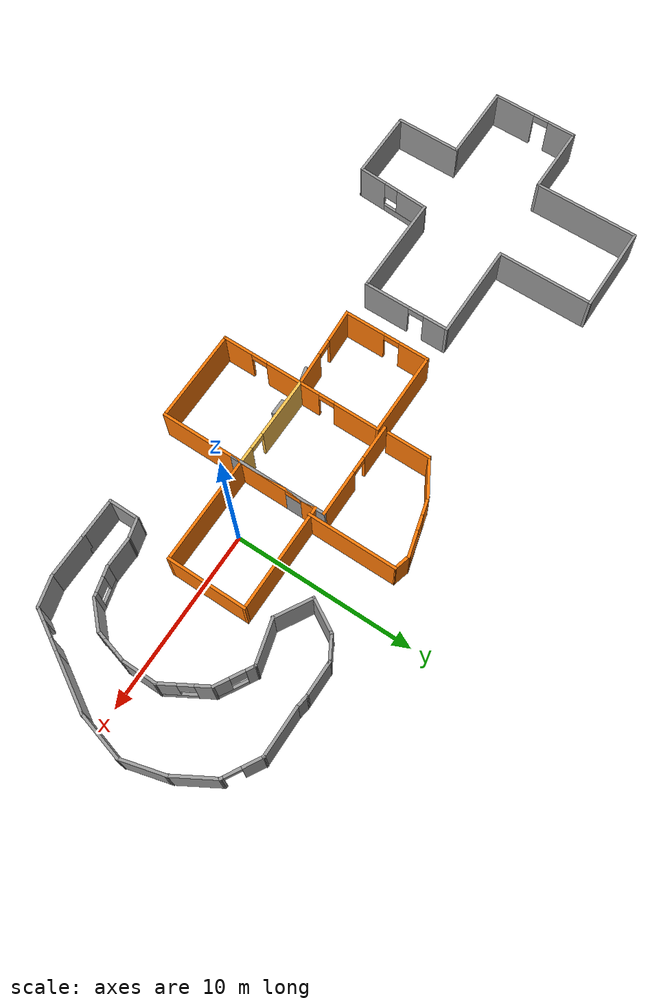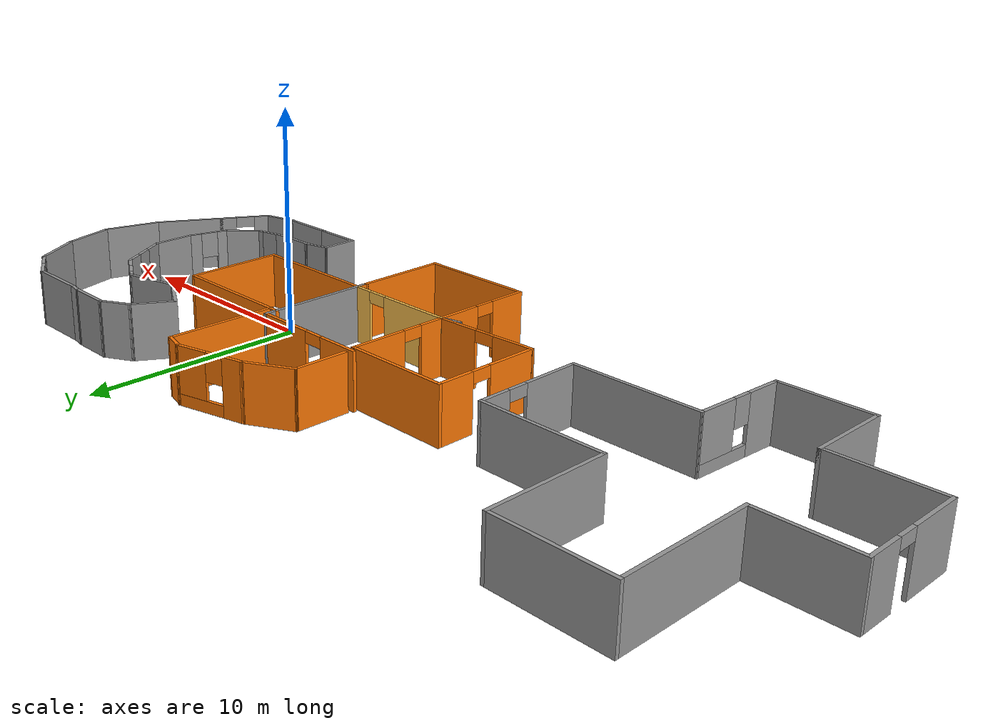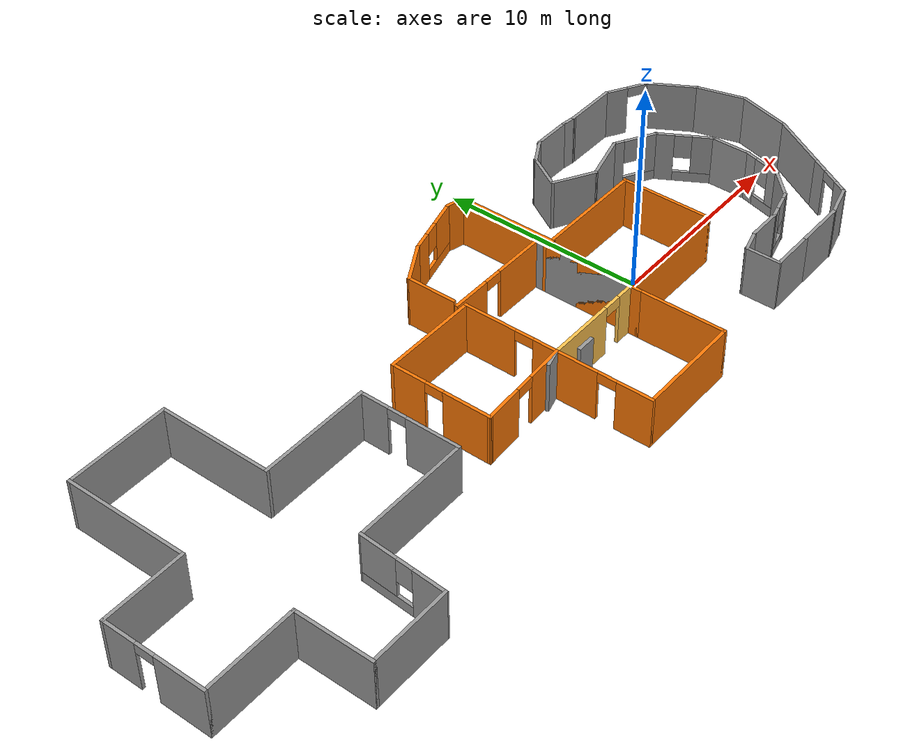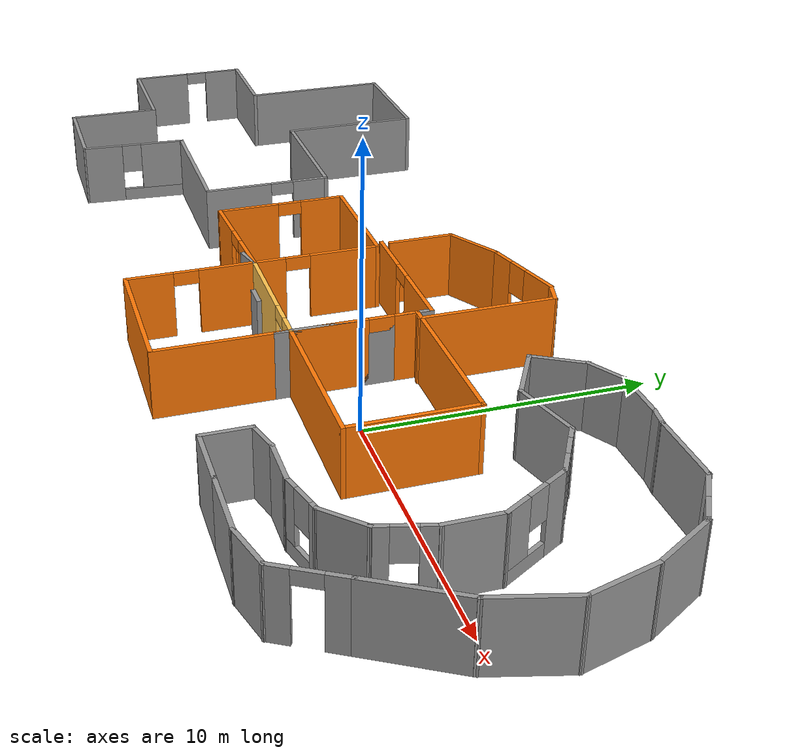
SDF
<?xml version='1.0'?>
<sdf version='1.6'>
  <model name='Cplusplus'>
    <pose frame=''>-8.29888 1.0832 0 0 -0 0</pose>
    <link name='Door_1'>
      <collision name='Door_1_Collision'>
        <geometry>
          <box>
            <size>0.9 0.17 2</size>
          </box>
        </geometry>
        <pose frame=''>0 0 1 0 -0 0</pose>
      </collision>
      <visual name='Door_1_Visual'>
        <pose frame=''>0 0 1 0 -0 0</pose>
        <geometry>
          <box>
            <size>0.9 0.17 2</size>
          </box>
        </geometry>
        <material>
          <script>
            <uri>file://media/materials/scripts/gazebo.material</uri>
            <name>Gazebo/Grey</name>
          </script>
        </material>
      </visual>
      <pose frame=''>2.05873 -2.95917 0 0 -0 0</pose>
    </link>
    <link name='Wall_10'>
      <pose frame=''>-4.07558 -0.465829 0 0 0 -1.5708</pose>
      <visual name='Wall_10_Visual_0'>
        <pose frame=''>-1.63477 0 1.25 0 -0 0</pose>
        <geometry>
          <box>
            <size>1.73046 0.15 2.5</size>
          </box>
        </geometry>
        <material>
          <script>
            <uri>file://media/materials/scripts/gazebo.material</uri>
            <name>Gazebo/Grey</name>
          </script>
          <ambient>0.996078 0.47451 0.0196078 1</ambient>
        </material>
        <meta>
          <layer>0</layer>
        </meta>
      </visual>
      <collision name='Wall_10_Collision_0'>
        <geometry>
          <box>
            <size>1.73046 0.15 2.5</size>
          </box>
        </geometry>
        <pose frame=''>-1.63477 0 1.25 0 -0 0</pose>
      </collision>
      <visual name='Wall_10_Visual_1'>
        <pose frame=''>1.31523 0 1.25 0 -0 0</pose>
        <geometry>
          <box>
            <size>2.36954 0.15 2.5</size>
          </box>
        </geometry>
        <material>
          <script>
            <uri>file://media/materials/scripts/gazebo.material</uri>
            <name>Gazebo/Grey</name>
          </script>
          <ambient>0.996078 0.47451 0.0196078 1</ambient>
        </material>
        <meta>
          <layer>0</layer>
        </meta>
      </visual>
      <collision name='Wall_10_Collision_1'>
        <geometry>
          <box>
            <size>2.36954 0.15 2.5</size>
          </box>
        </geometry>
        <pose frame=''>1.31523 0 1.25 0 -0 0</pose>
      </collision>
      <visual name='Wall_10_Visual_2'>
        <pose frame=''>-0.319538 0 2.25 0 -0 0</pose>
        <geometry>
          <box>
            <size>0.9 0.15 0.5</size>
          </box>
        </geometry>
        <material>
          <script>
            <uri>file://media/materials/scripts/gazebo.material</uri>
            <name>Gazebo/Grey</name>
          </script>
          <ambient>0.996078 0.47451 0.0196078 1</ambient>
        </material>
        <meta>
          <layer>0</layer>
        </meta>
      </visual>
      <collision name='Wall_10_Collision_2'>
        <geometry>
          <box>
            <size>0.9 0.15 0.5</size>
          </box>
        </geometry>
        <pose frame=''>-0.319538 0 2.25 0 -0 0</pose>
      </collision>
    </link>
    <link name='Wall_11'>
      <pose frame=''>-1.77558 -2.76583 0 0 -0 0.054294</pose>
      <visual name='Wall_11_Visual_0'>
        <pose frame=''>-1.40985 0 1.25 0 -0 0</pose>
        <geometry>
          <box>
            <size>1.9371 0.15 2.5</size>
          </box>
        </geometry>
        <material>
          <script>
            <uri>file://media/materials/scripts/gazebo.material</uri>
            <name>Gazebo/Grey</name>
          </script>
          <ambient>0.996078 0.47451 0.0196078 1</ambient>
        </material>
        <meta>
          <layer>0</layer>
        </meta>
      </visual>
      <collision name='Wall_11_Collision_0'>
        <geometry>
          <box>
            <size>1.9371 0.15 2.5</size>
          </box>
        </geometry>
        <pose frame=''>-1.40985 0 1.25 0 -0 0</pose>
      </collision>
      <visual name='Wall_11_Visual_1'>
        <pose frame=''>1.41855 0 1.25 0 -0 0</pose>
        <geometry>
          <box>
            <size>1.91969 0.15 2.5</size>
          </box>
        </geometry>
        <material>
          <script>
            <uri>file://media/materials/scripts/gazebo.material</uri>
            <name>Gazebo/Grey</name>
          </script>
          <ambient>0.996078 0.47451 0.0196078 1</ambient>
        </material>
        <meta>
          <layer>0</layer>
        </meta>
      </visual>
      <collision name='Wall_11_Collision_1'>
        <geometry>
          <box>
            <size>1.91969 0.15 2.5</size>
          </box>
        </geometry>
        <pose frame=''>1.41855 0 1.25 0 -0 0</pose>
      </collision>
      <visual name='Wall_11_Visual_2'>
        <pose frame=''>0.008704 0 2.25 0 -0 0</pose>
        <geometry>
          <box>
            <size>0.9 0.15 0.5</size>
          </box>
        </geometry>
        <material>
          <script>
            <uri>file://media/materials/scripts/gazebo.material</uri>
            <name>Gazebo/Grey</name>
          </script>
          <ambient>0.996078 0.47451 0.0196078 1</ambient>
        </material>
        <meta>
          <layer>0</layer>
        </meta>
      </visual>
      <collision name='Wall_11_Collision_2'>
        <geometry>
          <box>
            <size>0.9 0.15 0.5</size>
          </box>
        </geometry>
        <pose frame=''>0.008704 0 2.25 0 -0 0</pose>
      </collision>
    </link>
    <link name='Wall_12'>
      <collision name='Wall_12_Collision'>
        <geometry>
          <box>
            <size>1 0.15 2.5</size>
          </box>
        </geometry>
        <pose frame=''>0 0 1.25 0 -0 0</pose>
      </collision>
      <visual name='Wall_12_Visual'>
        <pose frame=''>0 0 1.25 0 -0 0</pose>
        <geometry>
          <box>
            <size>1 0.15 2.5</size>
          </box>
        </geometry>
        <material>
          <script>
            <uri>file://media/materials/scripts/gazebo.material</uri>
            <name>Gazebo/Grey</name>
          </script>
          <ambient>0 0 0 0</ambient>
        </material>
        <meta>
          <layer>0</layer>
        </meta>
      </visual>
      <pose frame=''>0.113905 -2.75083 0 0 0 -2.87979</pose>
    </link>
    <link name='Wall_13'>
      <pose frame=''>0.524424 -4.94083 0 0 0 -1.5708</pose>
      <visual name='Wall_13_Visual_0'>
        <pose frame=''>-1.32659 0 1.25 0 -0 0</pose>
        <geometry>
          <box>
            <size>2.09682 0.15 2.5</size>
          </box>
        </geometry>
        <material>
          <script>
            <uri>file://media/materials/scripts/gazebo.material</uri>
            <name>Gazebo/Grey</name>
          </script>
          <ambient>0.996078 0.47451 0.0196078 1</ambient>
        </material>
        <meta>
          <layer>0</layer>
        </meta>
      </visual>
      <collision name='Wall_13_Collision_0'>
        <geometry>
          <box>
            <size>2.09682 0.15 2.5</size>
          </box>
        </geometry>
        <pose frame=''>-1.32659 0 1.25 0 -0 0</pose>
      </collision>
      <visual name='Wall_13_Visual_1'>
        <pose frame=''>1.49841 0 1.25 0 -0 0</pose>
        <geometry>
          <box>
            <size>1.75318 0.15 2.5</size>
          </box>
        </geometry>
        <material>
          <script>
            <uri>file://media/materials/scripts/gazebo.material</uri>
            <name>Gazebo/Grey</name>
          </script>
          <ambient>0.996078 0.47451 0.0196078 1</ambient>
        </material>
        <meta>
          <layer>0</layer>
        </meta>
      </visual>
      <collision name='Wall_13_Collision_1'>
        <geometry>
          <box>
            <size>1.75318 0.15 2.5</size>
          </box>
        </geometry>
        <pose frame=''>1.49841 0 1.25 0 -0 0</pose>
      </collision>
      <visual name='Wall_13_Visual_2'>
        <pose frame=''>0.171817 0 2.25 0 -0 0</pose>
        <geometry>
          <box>
            <size>0.9 0.15 0.5</size>
          </box>
        </geometry>
        <material>
          <script>
            <uri>file://media/materials/scripts/gazebo.material</uri>
            <name>Gazebo/Grey</name>
          </script>
          <ambient>0.996078 0.47451 0.0196078 1</ambient>
        </material>
        <meta>
          <layer>0</layer>
        </meta>
      </visual>
      <collision name='Wall_13_Collision_2'>
        <geometry>
          <box>
            <size>0.9 0.15 0.5</size>
          </box>
        </geometry>
        <pose frame=''>0.171817 0 2.25 0 -0 0</pose>
      </collision>
    </link>
    <link name='Wall_14'>
      <collision name='Wall_14_Collision'>
        <geometry>
          <box>
            <size>5.25 0.15 2.5</size>
          </box>
        </geometry>
        <pose frame=''>0 0 1.25 0 -0 0</pose>
      </collision>
      <visual name='Wall_14_Visual'>
        <pose frame=''>0 0 1.25 0 -0 0</pose>
        <geometry>
          <box>
            <size>5.25 0.15 2.5</size>
          </box>
        </geometry>
        <material>
          <script>
            <uri>file://media/materials/scripts/gazebo.material</uri>
            <name>Gazebo/Grey</name>
          </script>
          <ambient>0.996078 0.47451 0.0196078 1</ambient>
        </material>
        <meta>
          <layer>0</layer>
        </meta>
      </visual>
      <pose frame=''>3.07442 -7.24083 0 0 -0 0</pose>
    </link>
    <link name='Wall_15'>
      <collision name='Wall_15_Collision'>
        <geometry>
          <box>
            <size>4.25 0.15 2.5</size>
          </box>
        </geometry>
        <pose frame=''>0 0 1.25 0 -0 0</pose>
      </collision>
      <visual name='Wall_15_Visual'>
        <pose frame=''>0 0 1.25 0 -0 0</pose>
        <geometry>
          <box>
            <size>4.25 0.15 2.5</size>
          </box>
        </geometry>
        <material>
          <script>
            <uri>file://media/materials/scripts/gazebo.material</uri>
            <name>Gazebo/Grey</name>
          </script>
          <ambient>0.996078 0.47451 0.0196078 1</ambient>
        </material>
        <meta>
          <layer>0</layer>
        </meta>
      </visual>
      <pose frame=''>5.62442 -5.19083 0 0 -0 1.5708</pose>
    </link>
    <link name='Wall_16'>
      <collision name='Wall_16_Collision'>
        <geometry>
          <box>
            <size>0.65 0.15 2.5</size>
          </box>
        </geometry>
        <pose frame=''>0 0 1.25 0 -0 0</pose>
      </collision>
      <visual name='Wall_16_Visual'>
        <pose frame=''>0 0 1.25 0 -0 0</pose>
        <geometry>
          <box>
            <size>0.65 0.15 2.5</size>
          </box>
        </geometry>
        <material>
          <script>
            <uri>file://media/materials/scripts/gazebo.material</uri>
            <name>Gazebo/Grey</name>
          </script>
          <ambient>1 1 1 1</ambient>
        </material>
        <meta>
          <layer>0</layer>
        </meta>
      </visual>
      <pose frame=''>5.62442 -2.89083 0 0 -0 1.5708</pose>
    </link>
    <link name='Wall_17'>
      <collision name='Wall_17_Collision'>
        <geometry>
          <box>
            <size>6 0.15 2.5</size>
          </box>
        </geometry>
        <pose frame=''>0 0 1.25 0 -0 0</pose>
      </collision>
      <visual name='Wall_17_Visual'>
        <pose frame=''>0 0 1.25 0 -0 0</pose>
        <geometry>
          <box>
            <size>6 0.15 2.5</size>
          </box>
        </geometry>
        <material>
          <script>
            <uri>file://media/materials/scripts/gazebo.material</uri>
            <name>Gazebo/Grey</name>
          </script>
          <ambient>0.996078 0.47451 0.0196078 1</ambient>
        </material>
        <meta>
          <layer>0</layer>
        </meta>
      </visual>
      <pose frame=''>8.54942 -2.64083 0 0 -0 0</pose>
    </link>
    <link name='Wall_18'>
      <collision name='Wall_18_Collision'>
        <geometry>
          <box>
            <size>4.5 0.15 2.5</size>
          </box>
        </geometry>
        <pose frame=''>0 0 1.25 0 -0 0</pose>
      </collision>
      <visual name='Wall_18_Visual'>
        <pose frame=''>0 0 1.25 0 -0 0</pose>
        <geometry>
          <box>
            <size>4.5 0.15 2.5</size>
          </box>
        </geometry>
        <material>
          <script>
            <uri>file://media/materials/scripts/gazebo.material</uri>
            <name>Gazebo/Grey</name>
          </script>
          <ambient>0.996078 0.47451 0.0196078 1</ambient>
        </material>
        <meta>
          <layer>0</layer>
        </meta>
      </visual>
      <pose frame=''>11.4744 -0.465829 0 0 -0 1.5708</pose>
    </link>
    <link name='Wall_19'>
      <collision name='Wall_19_Collision'>
        <geometry>
          <box>
            <size>6 0.15 2.5</size>
          </box>
        </geometry>
        <pose frame=''>0 0 1.25 0 -0 0</pose>
      </collision>
      <visual name='Wall_19_Visual'>
        <pose frame=''>0 0 1.25 0 -0 0</pose>
        <geometry>
          <box>
            <size>6 0.15 2.5</size>
          </box>
        </geometry>
        <material>
          <script>
            <uri>file://media/materials/scripts/gazebo.material</uri>
            <name>Gazebo/Grey</name>
          </script>
          <ambient>0.996078 0.47451 0.0196078 1</ambient>
        </material>
        <meta>
          <layer>0</layer>
        </meta>
      </visual>
      <pose frame=''>8.54942 1.70917 0 0 -0 3.14159</pose>
    </link>
    <link name='Wall_20'>
      <pose frame=''>5.62442 -0.715829 0 0 0 -1.5708</pose>
      <visual name='Wall_20_Visual_0'>
        <pose frame=''>-2.0582 0 1.25 0 -0 0</pose>
        <geometry>
          <box>
            <size>0.883603 0.15 2.5</size>
          </box>
        </geometry>
        <material>
          <script>
            <uri>file://media/materials/scripts/gazebo.material</uri>
            <name>Gazebo/Grey</name>
          </script>
          <ambient>0.996078 0.47451 0.0196078 1</ambient>
        </material>
        <meta>
          <layer>0</layer>
        </meta>
      </visual>
      <collision name='Wall_20_Collision_0'>
        <geometry>
          <box>
            <size>0.883603 0.15 2.5</size>
          </box>
        </geometry>
        <pose frame=''>-2.0582 0 1.25 0 -0 0</pose>
      </collision>
      <visual name='Wall_20_Visual_1'>
        <pose frame=''>0.891801 0 1.25 0 -0 0</pose>
        <geometry>
          <box>
            <size>3.2164 0.15 2.5</size>
          </box>
        </geometry>
        <material>
          <script>
            <uri>file://media/materials/scripts/gazebo.material</uri>
            <name>Gazebo/Grey</name>
          </script>
          <ambient>0.996078 0.47451 0.0196078 1</ambient>
        </material>
        <meta>
          <layer>0</layer>
        </meta>
      </visual>
      <collision name='Wall_20_Collision_1'>
        <geometry>
          <box>
            <size>3.2164 0.15 2.5</size>
          </box>
        </geometry>
        <pose frame=''>0.891801 0 1.25 0 -0 0</pose>
      </collision>
      <visual name='Wall_20_Visual_2'>
        <pose frame=''>-1.1664 0 2.25 0 -0 0</pose>
        <geometry>
          <box>
            <size>0.9 0.15 0.5</size>
          </box>
        </geometry>
        <material>
          <script>
            <uri>file://media/materials/scripts/gazebo.material</uri>
            <name>Gazebo/Grey</name>
          </script>
          <ambient>0.996078 0.47451 0.0196078 1</ambient>
        </material>
        <meta>
          <layer>0</layer>
        </meta>
      </visual>
      <collision name='Wall_20_Collision_2'>
        <geometry>
          <box>
            <size>0.9 0.15 0.5</size>
          </box>
        </geometry>
        <pose frame=''>-1.1664 0 2.25 0 -0 0</pose>
      </collision>
    </link>
    <link name='Wall_22'>
      <collision name='Wall_22_Collision'>
        <geometry>
          <box>
            <size>2.5 0.15 2.5</size>
          </box>
        </geometry>
        <pose frame=''>0 0 1.25 0 -0 0</pose>
      </collision>
      <visual name='Wall_22_Visual'>
        <pose frame=''>0 0 1.25 0 -0 0</pose>
        <geometry>
          <box>
            <size>2.5 0.15 2.5</size>
          </box>
        </geometry>
        <material>
          <script>
            <uri>file://media/materials/scripts/gazebo.material</uri>
            <name>Gazebo/Grey</name>
          </script>
          <ambient>0.996078 0.47451 0.0196078 1</ambient>
        </material>
        <meta>
          <layer>0</layer>
        </meta>
      </visual>
      <pose frame=''>0.39748 3.69181 0 0 -0 1.5708</pose>
    </link>
    <link name='Wall_23'>
      <collision name='Wall_23_Collision'>
        <geometry>
          <box>
            <size>2.25 0.15 2.5</size>
          </box>
        </geometry>
        <pose frame=''>0 0 1.25 0 -0 0</pose>
      </collision>
      <visual name='Wall_23_Visual'>
        <pose frame=''>0 0 1.25 0 -0 0</pose>
        <geometry>
          <box>
            <size>2.25 0.15 2.5</size>
          </box>
        </geometry>
        <material>
          <script>
            <uri>file://media/materials/scripts/gazebo.material</uri>
            <name>Gazebo/Grey</name>
          </script>
          <ambient>0.996078 0.47451 0.0196078 1</ambient>
        </material>
        <meta>
          <layer>0</layer>
        </meta>
      </visual>
      <pose frame=''>1.30681 5.39181 0 0 -0 0.523599</pose>
    </link>
    <link name='Wall_24'>
      <pose frame=''>3.71332 6.31798 0 0 -0 0.261799</pose>
      <visual name='Wall_24_Visual_0'>
        <pose frame=''>-1.12345 0 1.25 0 -0 0</pose>
        <geometry>
          <box>
            <size>1.00309 0.15 2.5</size>
          </box>
        </geometry>
        <material>
          <script>
            <uri>file://media/materials/scripts/gazebo.material</uri>
            <name>Gazebo/Grey</name>
          </script>
          <ambient>0.996078 0.47451 0.0196078 1</ambient>
        </material>
        <meta>
          <layer>0</layer>
        </meta>
      </visual>
      <collision name='Wall_24_Collision_0'>
        <geometry>
          <box>
            <size>1.00309 0.15 2.5</size>
          </box>
        </geometry>
        <pose frame=''>-1.12345 0 1.25 0 -0 0</pose>
      </collision>
      <visual name='Wall_24_Visual_1'>
        <pose frame=''>0.501546 0 0.25 0 -0 0</pose>
        <geometry>
          <box>
            <size>2.24691 0.15 0.5</size>
          </box>
        </geometry>
        <material>
          <script>
            <uri>file://media/materials/scripts/gazebo.material</uri>
            <name>Gazebo/Grey</name>
          </script>
          <ambient>0.996078 0.47451 0.0196078 1</ambient>
        </material>
        <meta>
          <layer>0</layer>
        </meta>
      </visual>
      <collision name='Wall_24_Collision_1'>
        <geometry>
          <box>
            <size>2.24691 0.15 0.5</size>
          </box>
        </geometry>
        <pose frame=''>0.501546 0 0.25 0 -0 0</pose>
      </collision>
      <visual name='Wall_24_Visual_2'>
        <pose frame=''>0.901546 0 1.5 0 -0 0</pose>
        <geometry>
          <box>
            <size>1.44691 0.15 2</size>
          </box>
        </geometry>
        <material>
          <script>
            <uri>file://media/materials/scripts/gazebo.material</uri>
            <name>Gazebo/Grey</name>
          </script>
          <ambient>0.996078 0.47451 0.0196078 1</ambient>
        </material>
        <meta>
          <layer>0</layer>
        </meta>
      </visual>
      <collision name='Wall_24_Collision_2'>
        <geometry>
          <box>
            <size>1.44691 0.15 2</size>
          </box>
        </geometry>
        <pose frame=''>0.901546 0 1.5 0 -0 0</pose>
      </collision>
      <visual name='Wall_24_Visual_3'>
        <pose frame=''>-0.221908 0 1.9 0 -0 0</pose>
        <geometry>
          <box>
            <size>0.8 0.15 1.2</size>
          </box>
        </geometry>
        <material>
          <script>
            <uri>file://media/materials/scripts/gazebo.material</uri>
            <name>Gazebo/Grey</name>
          </script>
          <ambient>0.996078 0.47451 0.0196078 1</ambient>
        </material>
        <meta>
          <layer>0</layer>
        </meta>
      </visual>
      <collision name='Wall_24_Collision_3'>
        <geometry>
          <box>
            <size>0.8 0.15 1.2</size>
          </box>
        </geometry>
        <pose frame=''>-0.221908 0 1.9 0 -0 0</pose>
      </collision>
    </link>
    <link name='Wall_25'>
      <collision name='Wall_25_Collision'>
        <geometry>
          <box>
            <size>1 0.15 2.5</size>
          </box>
        </geometry>
        <pose frame=''>0 0 1.25 0 -0 0</pose>
      </collision>
      <visual name='Wall_25_Visual'>
        <pose frame=''>0 0 1.25 0 -0 0</pose>
        <geometry>
          <box>
            <size>1 0.15 2.5</size>
          </box>
        </geometry>
        <material>
          <script>
            <uri>file://media/materials/scripts/gazebo.material</uri>
            <name>Gazebo/Grey</name>
          </script>
          <ambient>0.996078 0.47451 0.0196078 1</ambient>
        </material>
        <meta>
          <layer>0</layer>
        </meta>
      </visual>
      <pose frame=''>5.62102 6.60915 0 0 0 -0.261799</pose>
    </link>
    <link name='Wall_26'>
      <collision name='Wall_26_Collision'>
        <geometry>
          <box>
            <size>5 0.15 2.5</size>
          </box>
        </geometry>
        <pose frame=''>0 0 1.25 0 -0 0</pose>
      </collision>
      <visual name='Wall_26_Visual'>
        <pose frame=''>0 0 1.25 0 -0 0</pose>
        <geometry>
          <box>
            <size>5 0.15 2.5</size>
          </box>
        </geometry>
        <material>
          <script>
            <uri>file://media/materials/scripts/gazebo.material</uri>
            <name>Gazebo/Grey</name>
          </script>
          <ambient>0.996078 0.47451 0.0196078 1</ambient>
        </material>
        <meta>
          <layer>0</layer>
        </meta>
      </visual>
      <pose frame=''>6.03154 4.07415 0 0 0 -1.5708</pose>
    </link>
    <link name='Wall_28'>
      <collision name='Wall_28_Collision'>
        <geometry>
          <box>
            <size>2 0.15 2.5</size>
          </box>
        </geometry>
        <pose frame=''>0 0 1.25 0 -0 0</pose>
      </collision>
      <visual name='Wall_28_Visual'>
        <pose frame=''>0 0 1.25 0 -0 0</pose>
        <geometry>
          <box>
            <size>2 0.15 2.5</size>
          </box>
        </geometry>
        <material>
          <script>
            <uri>file://media/materials/scripts/gazebo.material</uri>
            <name>Gazebo/Grey</name>
          </script>
          <ambient>1 1 1 1</ambient>
        </material>
        <meta>
          <layer>0</layer>
        </meta>
      </visual>
      <pose frame=''>12.3318 6.39307 0 0 -0 3.14159</pose>
    </link>
    <link name='Wall_29'>
      <collision name='Wall_29_Collision'>
        <geometry>
          <box>
            <size>1.5 0.15 2.5</size>
          </box>
        </geometry>
        <pose frame=''>0 0 1.25 0 -0 0</pose>
      </collision>
      <visual name='Wall_29_Visual'>
        <pose frame=''>0 0 1.25 0 -0 0</pose>
        <geometry>
          <box>
            <size>1.5 0.15 2.5</size>
          </box>
        </geometry>
        <material>
          <script>
            <uri>file://media/materials/scripts/gazebo.material</uri>
            <name>Gazebo/Grey</name>
          </script>
          <ambient>1 1 1 1</ambient>
        </material>
        <meta>
          <layer>0</layer>
        </meta>
      </visual>
      <pose frame=''>10.8222 6.05557 0 0 0 -2.61799</pose>
    </link>
    <link name='Wall_30'>
      <collision name='Wall_30_Collision'>
        <geometry>
          <box>
            <size>2 0.15 2.5</size>
          </box>
        </geometry>
        <pose frame=''>0 0 1.25 0 -0 0</pose>
      </collision>
      <visual name='Wall_30_Visual'>
        <pose frame=''>0 0 1.25 0 -0 0</pose>
        <geometry>
          <box>
            <size>2 0.15 2.5</size>
          </box>
        </geometry>
        <material>
          <script>
            <uri>file://media/materials/scripts/gazebo.material</uri>
            <name>Gazebo/Grey</name>
          </script>
          <ambient>1 1 1 1</ambient>
        </material>
        <meta>
          <layer>0</layer>
        </meta>
      </visual>
      <pose frame=''>9.77517 4.91699 0 0 0 -2.0944</pose>
    </link>
    <link name='Wall_31'>
      <collision name='Wall_31_Collision'>
        <geometry>
          <box>
            <size>2.25 0.15 2.5</size>
          </box>
        </geometry>
        <pose frame=''>0 0 1.25 0 -0 0</pose>
      </collision>
      <visual name='Wall_31_Visual'>
        <pose frame=''>0 0 1.25 0 -0 0</pose>
        <geometry>
          <box>
            <size>2.25 0.15 2.5</size>
          </box>
        </geometry>
        <material>
          <script>
            <uri>file://media/materials/scripts/gazebo.material</uri>
            <name>Gazebo/Grey</name>
          </script>
          <ambient>1 1 1 1</ambient>
        </material>
        <meta>
          <layer>0</layer>
        </meta>
      </visual>
      <pose frame=''>10.222 3.59092 0 0 0 -0.523599</pose>
    </link>
    <link name='Wall_32'>
      <collision name='Wall_32_Collision'>
        <geometry>
          <box>
            <size>2.5 0.15 2.5</size>
          </box>
        </geometry>
        <pose frame=''>0 0 1.25 0 -0 0</pose>
      </collision>
      <visual name='Wall_32_Visual'>
        <pose frame=''>0 0 1.25 0 -0 0</pose>
        <geometry>
          <box>
            <size>2.5 0.15 2.5</size>
          </box>
        </geometry>
        <material>
          <script>
            <uri>file://media/materials/scripts/gazebo.material</uri>
            <name>Gazebo/Grey</name>
          </script>
          <ambient>1 1 1 1</ambient>
        </material>
        <meta>
          <layer>0</layer>
        </meta>
      </visual>
      <pose frame=''>12.2663 3.37003 0 0 -0 0.261799</pose>
    </link>
    <link name='Wall_33'>
      <pose frame=''>14.3106 3.14914 0 0 0 -0.523599</pose>
      <visual name='Wall_33_Visual_0'>
        <pose frame=''>-0.843094 0 1.25 0 -0 0</pose>
        <geometry>
          <box>
            <size>0.563813 0.15 2.5</size>
          </box>
        </geometry>
        <material>
          <script>
            <uri>file://media/materials/scripts/gazebo.material</uri>
            <name>Gazebo/Grey</name>
          </script>
          <ambient>1 1 1 1</ambient>
        </material>
        <meta>
          <layer>0</layer>
        </meta>
      </visual>
      <collision name='Wall_33_Collision_0'>
        <geometry>
          <box>
            <size>0.563813 0.15 2.5</size>
          </box>
        </geometry>
        <pose frame=''>-0.843094 0 1.25 0 -0 0</pose>
      </collision>
      <visual name='Wall_33_Visual_1'>
        <pose frame=''>0.281906 0 0.25 0 -0 0</pose>
        <geometry>
          <box>
            <size>1.68619 0.15 0.5</size>
          </box>
        </geometry>
        <material>
          <script>
            <uri>file://media/materials/scripts/gazebo.material</uri>
            <name>Gazebo/Grey</name>
          </script>
          <ambient>1 1 1 1</ambient>
        </material>
        <meta>
          <layer>0</layer>
        </meta>
      </visual>
      <collision name='Wall_33_Collision_1'>
        <geometry>
          <box>
            <size>1.68619 0.15 0.5</size>
          </box>
        </geometry>
        <pose frame=''>0.281906 0 0.25 0 -0 0</pose>
      </collision>
      <visual name='Wall_33_Visual_2'>
        <pose frame=''>0.681906 0 1.5 0 -0 0</pose>
        <geometry>
          <box>
            <size>0.886187 0.15 2</size>
          </box>
        </geometry>
        <material>
          <script>
            <uri>file://media/materials/scripts/gazebo.material</uri>
            <name>Gazebo/Grey</name>
          </script>
          <ambient>1 1 1 1</ambient>
        </material>
        <meta>
          <layer>0</layer>
        </meta>
      </visual>
      <collision name='Wall_33_Collision_2'>
        <geometry>
          <box>
            <size>0.886187 0.15 2</size>
          </box>
        </geometry>
        <pose frame=''>0.681906 0 1.5 0 -0 0</pose>
      </collision>
      <visual name='Wall_33_Visual_3'>
        <pose frame=''>-0.161187 0 1.9 0 -0 0</pose>
        <geometry>
          <box>
            <size>0.8 0.15 1.2</size>
          </box>
        </geometry>
        <material>
          <script>
            <uri>file://media/materials/scripts/gazebo.material</uri>
            <name>Gazebo/Grey</name>
          </script>
          <ambient>1 1 1 1</ambient>
        </material>
        <meta>
          <layer>0</layer>
        </meta>
      </visual>
      <collision name='Wall_33_Collision_3'>
        <geometry>
          <box>
            <size>0.8 0.15 1.2</size>
          </box>
        </geometry>
        <pose frame=''>-0.161187 0 1.9 0 -0 0</pose>
      </collision>
    </link>
    <link name='Wall_34'>
      <pose frame=''>15.8699 1.49831 0 0 0 -1.0472</pose>
      <visual name='Wall_34_Visual_0'>
        <pose frame=''>-0.914638 0 1.25 0 -0 0</pose>
        <geometry>
          <box>
            <size>0.920725 0.15 2.5</size>
          </box>
        </geometry>
        <material>
          <script>
            <uri>file://media/materials/scripts/gazebo.material</uri>
            <name>Gazebo/Grey</name>
          </script>
          <ambient>1 1 1 1</ambient>
        </material>
        <meta>
          <layer>0</layer>
        </meta>
      </visual>
      <collision name='Wall_34_Collision_0'>
        <geometry>
          <box>
            <size>0.920725 0.15 2.5</size>
          </box>
        </geometry>
        <pose frame=''>-0.914638 0 1.25 0 -0 0</pose>
      </collision>
      <visual name='Wall_34_Visual_1'>
        <pose frame=''>0.460362 0 0.25 0 -0 0</pose>
        <geometry>
          <box>
            <size>1.82927 0.15 0.5</size>
          </box>
        </geometry>
        <material>
          <script>
            <uri>file://media/materials/scripts/gazebo.material</uri>
            <name>Gazebo/Grey</name>
          </script>
          <ambient>1 1 1 1</ambient>
        </material>
        <meta>
          <layer>0</layer>
        </meta>
      </visual>
      <collision name='Wall_34_Collision_1'>
        <geometry>
          <box>
            <size>1.82927 0.15 0.5</size>
          </box>
        </geometry>
        <pose frame=''>0.460362 0 0.25 0 -0 0</pose>
      </collision>
      <visual name='Wall_34_Visual_2'>
        <pose frame=''>0.860362 0 1.5 0 -0 0</pose>
        <geometry>
          <box>
            <size>1.02927 0.15 2</size>
          </box>
        </geometry>
        <material>
          <script>
            <uri>file://media/materials/scripts/gazebo.material</uri>
            <name>Gazebo/Grey</name>
          </script>
          <ambient>1 1 1 1</ambient>
        </material>
        <meta>
          <layer>0</layer>
        </meta>
      </visual>
      <collision name='Wall_34_Collision_2'>
        <geometry>
          <box>
            <size>1.02927 0.15 2</size>
          </box>
        </geometry>
        <pose frame=''>0.860362 0 1.5 0 -0 0</pose>
      </collision>
      <visual name='Wall_34_Visual_3'>
        <pose frame=''>-0.054275 0 1.9 0 -0 0</pose>
        <geometry>
          <box>
            <size>0.8 0.15 1.2</size>
          </box>
        </geometry>
        <material>
          <script>
            <uri>file://media/materials/scripts/gazebo.material</uri>
            <name>Gazebo/Grey</name>
          </script>
          <ambient>1 1 1 1</ambient>
        </material>
        <meta>
          <layer>0</layer>
        </meta>
      </visual>
      <collision name='Wall_34_Collision_3'>
        <geometry>
          <box>
            <size>0.8 0.15 1.2</size>
          </box>
        </geometry>
        <pose frame=''>-0.054275 0 1.9 0 -0 0</pose>
      </collision>
    </link>
    <link name='Wall_35'>
      <collision name='Wall_35_Collision'>
        <geometry>
          <box>
            <size>2 0.15 2.5</size>
          </box>
        </geometry>
        <pose frame=''>0 0 1.25 0 -0 0</pose>
      </collision>
      <visual name='Wall_35_Visual'>
        <pose frame=''>0 0 1.25 0 -0 0</pose>
        <geometry>
          <box>
            <size>2 0.15 2.5</size>
          </box>
        </geometry>
        <material>
          <script>
            <uri>file://media/materials/scripts/gazebo.material</uri>
            <name>Gazebo/Grey</name>
          </script>
          <ambient>1 1 1 1</ambient>
        </material>
        <meta>
          <layer>0</layer>
        </meta>
      </visual>
      <pose frame=''>16.5199 -0.552522 0 0 0 -1.5708</pose>
    </link>
    <link name='Wall_36'>
      <pose frame=''>16.2805 -2.371 0 0 0 -1.8326</pose>
      <visual name='Wall_36_Visual_0'>
        <pose frame=''>-0.686343 0 1.25 0 -0 0</pose>
        <geometry>
          <box>
            <size>0.627315 0.15 2.5</size>
          </box>
        </geometry>
        <material>
          <script>
            <uri>file://media/materials/scripts/gazebo.material</uri>
            <name>Gazebo/Grey</name>
          </script>
          <ambient>1 1 1 1</ambient>
        </material>
        <meta>
          <layer>0</layer>
        </meta>
      </visual>
      <collision name='Wall_36_Collision_0'>
        <geometry>
          <box>
            <size>0.627315 0.15 2.5</size>
          </box>
        </geometry>
        <pose frame=''>-0.686343 0 1.25 0 -0 0</pose>
      </collision>
      <visual name='Wall_36_Visual_1'>
        <pose frame=''>0.313657 0 0.25 0 -0 0</pose>
        <geometry>
          <box>
            <size>1.37268 0.15 0.5</size>
          </box>
        </geometry>
        <material>
          <script>
            <uri>file://media/materials/scripts/gazebo.material</uri>
            <name>Gazebo/Grey</name>
          </script>
          <ambient>1 1 1 1</ambient>
        </material>
        <meta>
          <layer>0</layer>
        </meta>
      </visual>
      <collision name='Wall_36_Collision_1'>
        <geometry>
          <box>
            <size>1.37268 0.15 0.5</size>
          </box>
        </geometry>
        <pose frame=''>0.313657 0 0.25 0 -0 0</pose>
      </collision>
      <visual name='Wall_36_Visual_2'>
        <pose frame=''>0.713657 0 1.5 0 -0 0</pose>
        <geometry>
          <box>
            <size>0.572685 0.15 2</size>
          </box>
        </geometry>
        <material>
          <script>
            <uri>file://media/materials/scripts/gazebo.material</uri>
            <name>Gazebo/Grey</name>
          </script>
          <ambient>1 1 1 1</ambient>
        </material>
        <meta>
          <layer>0</layer>
        </meta>
      </visual>
      <collision name='Wall_36_Collision_2'>
        <geometry>
          <box>
            <size>0.572685 0.15 2</size>
          </box>
        </geometry>
        <pose frame=''>0.713657 0 1.5 0 -0 0</pose>
      </collision>
      <visual name='Wall_36_Visual_3'>
        <pose frame=''>0.027315 0 1.9 0 -0 0</pose>
        <geometry>
          <box>
            <size>0.8 0.15 1.2</size>
          </box>
        </geometry>
        <material>
          <script>
            <uri>file://media/materials/scripts/gazebo.material</uri>
            <name>Gazebo/Grey</name>
          </script>
          <ambient>1 1 1 1</ambient>
        </material>
        <meta>
          <layer>0</layer>
        </meta>
      </visual>
      <collision name='Wall_36_Collision_3'>
        <geometry>
          <box>
            <size>0.8 0.15 1.2</size>
          </box>
        </geometry>
        <pose frame=''>0.027315 0 1.9 0 -0 0</pose>
      </collision>
    </link>
    <link name='Wall_37'>
      <collision name='Wall_37_Collision'>
        <geometry>
          <box>
            <size>1.75 0.15 2.5</size>
          </box>
        </geometry>
        <pose frame=''>0 0 1.25 0 -0 0</pose>
      </collision>
      <visual name='Wall_37_Visual'>
        <pose frame=''>0 0 1.25 0 -0 0</pose>
        <geometry>
          <box>
            <size>1.75 0.15 2.5</size>
          </box>
        </geometry>
        <material>
          <script>
            <uri>file://media/materials/scripts/gazebo.material</uri>
            <name>Gazebo/Grey</name>
          </script>
          <ambient>1 1 1 1</ambient>
        </material>
        <meta>
          <layer>0</layer>
        </meta>
      </visual>
      <pose frame=''>15.4754 -3.83017 0 0 0 -2.35619</pose>
    </link>
    <link name='Wall_38'>
      <pose frame=''>14.137 -4.60291 0 0 0 -2.87979</pose>
      <visual name='Wall_38_Visual_0'>
        <pose frame=''>-0.70207 0 1.25 0 -0 0</pose>
        <geometry>
          <box>
            <size>0.34586 0.15 2.5</size>
          </box>
        </geometry>
        <material>
          <script>
            <uri>file://media/materials/scripts/gazebo.material</uri>
            <name>Gazebo/Grey</name>
          </script>
          <ambient>1 1 1 1</ambient>
        </material>
        <meta>
          <layer>0</layer>
        </meta>
      </visual>
      <collision name='Wall_38_Collision_0'>
        <geometry>
          <box>
            <size>0.34586 0.15 2.5</size>
          </box>
        </geometry>
        <pose frame=''>-0.70207 0 1.25 0 -0 0</pose>
      </collision>
      <visual name='Wall_38_Visual_1'>
        <pose frame=''>0.17293 0 0.25 0 -0 0</pose>
        <geometry>
          <box>
            <size>1.40414 0.15 0.5</size>
          </box>
        </geometry>
        <material>
          <script>
            <uri>file://media/materials/scripts/gazebo.material</uri>
            <name>Gazebo/Grey</name>
          </script>
          <ambient>1 1 1 1</ambient>
        </material>
        <meta>
          <layer>0</layer>
        </meta>
      </visual>
      <collision name='Wall_38_Collision_1'>
        <geometry>
          <box>
            <size>1.40414 0.15 0.5</size>
          </box>
        </geometry>
        <pose frame=''>0.17293 0 0.25 0 -0 0</pose>
      </collision>
      <visual name='Wall_38_Visual_2'>
        <pose frame=''>0.57293 0 1.5 0 -0 0</pose>
        <geometry>
          <box>
            <size>0.60414 0.15 2</size>
          </box>
        </geometry>
        <material>
          <script>
            <uri>file://media/materials/scripts/gazebo.material</uri>
            <name>Gazebo/Grey</name>
          </script>
          <ambient>1 1 1 1</ambient>
        </material>
        <meta>
          <layer>0</layer>
        </meta>
      </visual>
      <collision name='Wall_38_Collision_2'>
        <geometry>
          <box>
            <size>0.60414 0.15 2</size>
          </box>
        </geometry>
        <pose frame=''>0.57293 0 1.5 0 -0 0</pose>
      </collision>
      <visual name='Wall_38_Visual_3'>
        <pose frame=''>-0.12914 0 1.9 0 -0 0</pose>
        <geometry>
          <box>
            <size>0.8 0.15 1.2</size>
          </box>
        </geometry>
        <material>
          <script>
            <uri>file://media/materials/scripts/gazebo.material</uri>
            <name>Gazebo/Grey</name>
          </script>
          <ambient>1 1 1 1</ambient>
        </material>
        <meta>
          <layer>0</layer>
        </meta>
      </visual>
      <collision name='Wall_38_Collision_3'>
        <geometry>
          <box>
            <size>0.8 0.15 1.2</size>
          </box>
        </geometry>
        <pose frame=''>-0.12914 0 1.9 0 -0 0</pose>
      </collision>
    </link>
    <link name='Wall_39'>
      <collision name='Wall_39_Collision'>
        <geometry>
          <box>
            <size>1.75 0.15 2.5</size>
          </box>
        </geometry>
        <pose frame=''>0 0 1.25 0 -0 0</pose>
      </collision>
      <visual name='Wall_39_Visual'>
        <pose frame=''>0 0 1.25 0 -0 0</pose>
        <geometry>
          <box>
            <size>1.75 0.15 2.5</size>
          </box>
        </geometry>
        <material>
          <script>
            <uri>file://media/materials/scripts/gazebo.material</uri>
            <name>Gazebo/Grey</name>
          </script>
          <ambient>1 1 1 1</ambient>
        </material>
        <meta>
          <layer>0</layer>
        </meta>
      </visual>
      <pose frame=''>12.5642 -4.80997 0 0 -0 3.14159</pose>
    </link>
    <link name='Wall_40'>
      <collision name='Wall_40_Collision'>
        <geometry>
          <box>
            <size>1.25 0.15 2.5</size>
          </box>
        </geometry>
        <pose frame=''>0 0 1.25 0 -0 0</pose>
      </collision>
      <visual name='Wall_40_Visual'>
        <pose frame=''>0 0 1.25 0 -0 0</pose>
        <geometry>
          <box>
            <size>1.25 0.15 2.5</size>
          </box>
        </geometry>
        <material>
          <script>
            <uri>file://media/materials/scripts/gazebo.material</uri>
            <name>Gazebo/Grey</name>
          </script>
          <ambient>1 1 1 1</ambient>
        </material>
        <meta>
          <layer>0</layer>
        </meta>
      </visual>
      <pose frame=''>11.233 -4.95232 0 0 0 -2.87979</pose>
    </link>
    <link name='Wall_41'>
      <collision name='Wall_41_Collision'>
        <geometry>
          <box>
            <size>1.75 0.15 2.5</size>
          </box>
        </geometry>
        <pose frame=''>0 0 1.25 0 -0 0</pose>
      </collision>
      <visual name='Wall_41_Visual'>
        <pose frame=''>0 0 1.25 0 -0 0</pose>
        <geometry>
          <box>
            <size>1.75 0.15 2.5</size>
          </box>
        </geometry>
        <material>
          <script>
            <uri>file://media/materials/scripts/gazebo.material</uri>
            <name>Gazebo/Grey</name>
          </script>
          <ambient>1 1 1 1</ambient>
        </material>
        <meta>
          <layer>0</layer>
        </meta>
      </visual>
      <pose frame=''>10.7017 -5.89467 0 0 0 -1.5708</pose>
    </link>
    <link name='Wall_42'>
      <collision name='Wall_42_Collision'>
        <geometry>
          <box>
            <size>2.25 0.15 2.5</size>
          </box>
        </geometry>
        <pose frame=''>0 0 1.25 0 -0 0</pose>
      </collision>
      <visual name='Wall_42_Visual'>
        <pose frame=''>0 0 1.25 0 -0 0</pose>
        <geometry>
          <box>
            <size>2.25 0.15 2.5</size>
          </box>
        </geometry>
        <material>
          <script>
            <uri>file://media/materials/scripts/gazebo.material</uri>
            <name>Gazebo/Grey</name>
          </script>
          <ambient>1 1 1 1</ambient>
        </material>
        <meta>
          <layer>0</layer>
        </meta>
      </visual>
      <pose frame=''>11.7517 -6.69467 0 0 -0 0</pose>
    </link>
    <link name='Wall_43'>
      <collision name='Wall_43_Collision'>
        <geometry>
          <box>
            <size>2.5 0.15 2.5</size>
          </box>
        </geometry>
        <pose frame=''>0 0 1.25 0 -0 0</pose>
      </collision>
      <visual name='Wall_43_Visual'>
        <pose frame=''>0 0 1.25 0 -0 0</pose>
        <geometry>
          <box>
            <size>2.5 0.15 2.5</size>
          </box>
        </geometry>
        <material>
          <script>
            <uri>file://media/materials/scripts/gazebo.material</uri>
            <name>Gazebo/Grey</name>
          </script>
          <ambient>1 1 1 1</ambient>
        </material>
        <meta>
          <layer>0</layer>
        </meta>
      </visual>
      <pose frame=''>13.9767 -6.69467 0 0 -0 0</pose>
    </link>
    <link name='Wall_44'>
      <collision name='Wall_44_Collision'>
        <geometry>
          <box>
            <size>1.75 0.15 2.5</size>
          </box>
        </geometry>
        <pose frame=''>0 0 1.25 0 -0 0</pose>
      </collision>
      <visual name='Wall_44_Visual'>
        <pose frame=''>0 0 1.25 0 -0 0</pose>
        <geometry>
          <box>
            <size>1.75 0.15 2.5</size>
          </box>
        </geometry>
        <material>
          <script>
            <uri>file://media/materials/scripts/gazebo.material</uri>
            <name>Gazebo/Grey</name>
          </script>
          <ambient>1 1 1 1</ambient>
        </material>
        <meta>
          <layer>0</layer>
        </meta>
      </visual>
      <pose frame=''>15.9245 -6.48761 0 0 -0 0.261799</pose>
    </link>
    <link name='Wall_45'>
      <pose frame=''>17.2847 -5.26298 0 0 -0 1.0472</pose>
      <visual name='Wall_45_Visual_0'>
        <pose frame=''>-0.860729 0 1.25 0 -0 0</pose>
        <geometry>
          <box>
            <size>0.778542 0.15 2.5</size>
          </box>
        </geometry>
        <material>
          <script>
            <uri>file://media/materials/scripts/gazebo.material</uri>
            <name>Gazebo/Grey</name>
          </script>
          <ambient>1 1 1 1</ambient>
        </material>
        <meta>
          <layer>0</layer>
        </meta>
      </visual>
      <collision name='Wall_45_Collision_0'>
        <geometry>
          <box>
            <size>0.778542 0.15 2.5</size>
          </box>
        </geometry>
        <pose frame=''>-0.860729 0 1.25 0 -0 0</pose>
      </collision>
      <visual name='Wall_45_Visual_1'>
        <pose frame=''>0.839271 0 1.25 0 -0 0</pose>
        <geometry>
          <box>
            <size>0.821458 0.15 2.5</size>
          </box>
        </geometry>
        <material>
          <script>
            <uri>file://media/materials/scripts/gazebo.material</uri>
            <name>Gazebo/Grey</name>
          </script>
          <ambient>1 1 1 1</ambient>
        </material>
        <meta>
          <layer>0</layer>
        </meta>
      </visual>
      <collision name='Wall_45_Collision_1'>
        <geometry>
          <box>
            <size>0.821458 0.15 2.5</size>
          </box>
        </geometry>
        <pose frame=''>0.839271 0 1.25 0 -0 0</pose>
      </collision>
      <visual name='Wall_45_Visual_2'>
        <pose frame=''>-0.021458 0 2.25 0 -0 0</pose>
        <geometry>
          <box>
            <size>0.9 0.15 0.5</size>
          </box>
        </geometry>
        <material>
          <script>
            <uri>file://media/materials/scripts/gazebo.material</uri>
            <name>Gazebo/Grey</name>
          </script>
          <ambient>1 1 1 1</ambient>
        </material>
        <meta>
          <layer>0</layer>
        </meta>
      </visual>
      <collision name='Wall_45_Collision_2'>
        <geometry>
          <box>
            <size>0.9 0.15 0.5</size>
          </box>
        </geometry>
        <pose frame=''>-0.021458 0 2.25 0 -0 0</pose>
      </collision>
    </link>
    <link name='Wall_46'>
      <collision name='Wall_46_Collision'>
        <geometry>
          <box>
            <size>3.25 0.15 2.5</size>
          </box>
        </geometry>
        <pose frame=''>0 0 1.25 0 -0 0</pose>
      </collision>
      <visual name='Wall_46_Visual'>
        <pose frame=''>0 0 1.25 0 -0 0</pose>
        <geometry>
          <box>
            <size>3.25 0.15 2.5</size>
          </box>
        </geometry>
        <material>
          <script>
            <uri>file://media/materials/scripts/gazebo.material</uri>
            <name>Gazebo/Grey</name>
          </script>
          <ambient>1 1 1 1</ambient>
        </material>
        <meta>
          <layer>0</layer>
        </meta>
      </visual>
      <pose frame=''>18.6472 -2.90306 0 0 -0 1.0472</pose>
    </link>
    <link name='Wall_47'>
      <collision name='Wall_47_Collision'>
        <geometry>
          <box>
            <size>2.75 0.15 2.5</size>
          </box>
        </geometry>
        <pose frame=''>0 0 1.25 0 -0 0</pose>
      </collision>
      <visual name='Wall_47_Visual'>
        <pose frame=''>0 0 1.25 0 -0 0</pose>
        <geometry>
          <box>
            <size>2.75 0.15 2.5</size>
          </box>
        </geometry>
        <material>
          <script>
            <uri>file://media/materials/scripts/gazebo.material</uri>
            <name>Gazebo/Grey</name>
          </script>
          <ambient>1 1 1 1</ambient>
        </material>
        <meta>
          <layer>0</layer>
        </meta>
      </visual>
      <pose frame=''>19.7587 -0.305015 0 0 -0 1.309</pose>
    </link>
    <link name='Wall_48'>
      <collision name='Wall_48_Collision'>
        <geometry>
          <box>
            <size>2.5 0.15 2.5</size>
          </box>
        </geometry>
        <pose frame=''>0 0 1.25 0 -0 0</pose>
      </collision>
      <visual name='Wall_48_Visual'>
        <pose frame=''>0 0 1.25 0 -0 0</pose>
        <geometry>
          <box>
            <size>2.5 0.15 2.5</size>
          </box>
        </geometry>
        <material>
          <script>
            <uri>file://media/materials/scripts/gazebo.material</uri>
            <name>Gazebo/Grey</name>
          </script>
          <ambient>1 1 1 1</ambient>
        </material>
        <meta>
          <layer>0</layer>
        </meta>
      </visual>
      <pose frame=''>19.791 2.08565 0 0 -0 1.8326</pose>
    </link>
    <link name='Wall_49'>
      <collision name='Wall_49_Collision'>
        <geometry>
          <box>
            <size>2.5 0.15 2.5</size>
          </box>
        </geometry>
        <pose frame=''>0 0 1.25 0 -0 0</pose>
      </collision>
      <visual name='Wall_49_Visual'>
        <pose frame=''>0 0 1.25 0 -0 0</pose>
        <geometry>
          <box>
            <size>2.5 0.15 2.5</size>
          </box>
        </geometry>
        <material>
          <script>
            <uri>file://media/materials/scripts/gazebo.material</uri>
            <name>Gazebo/Grey</name>
          </script>
          <ambient>1 1 1 1</ambient>
        </material>
        <meta>
          <layer>0</layer>
        </meta>
      </visual>
      <pose frame=''>18.8994 4.23819 0 0 -0 2.0944</pose>
    </link>
    <link name='Wall_5'>
      <pose frame=''>2.94942 2.20917 0 0 -0 0</pose>
      <visual name='Wall_5_Visual_0'>
        <pose frame=''>-1.76993 0 1.25 0 -0 0</pose>
        <geometry>
          <box>
            <size>1.96013 0.15 2.5</size>
          </box>
        </geometry>
        <material>
          <script>
            <uri>file://media/materials/scripts/gazebo.material</uri>
            <name>Gazebo/Grey</name>
          </script>
          <ambient>0.996078 0.47451 0.0196078 1</ambient>
        </material>
        <meta>
          <layer>0</layer>
        </meta>
      </visual>
      <collision name='Wall_5_Collision_0'>
        <geometry>
          <box>
            <size>1.96013 0.15 2.5</size>
          </box>
        </geometry>
        <pose frame=''>-1.76993 0 1.25 0 -0 0</pose>
      </collision>
      <visual name='Wall_5_Visual_1'>
        <pose frame=''>1.43007 0 1.25 0 -0 0</pose>
        <geometry>
          <box>
            <size>2.63987 0.15 2.5</size>
          </box>
        </geometry>
        <material>
          <script>
            <uri>file://media/materials/scripts/gazebo.material</uri>
            <name>Gazebo/Grey</name>
          </script>
          <ambient>0.996078 0.47451 0.0196078 1</ambient>
        </material>
        <meta>
          <layer>0</layer>
        </meta>
      </visual>
      <collision name='Wall_5_Collision_1'>
        <geometry>
          <box>
            <size>2.63987 0.15 2.5</size>
          </box>
        </geometry>
        <pose frame=''>1.43007 0 1.25 0 -0 0</pose>
      </collision>
      <visual name='Wall_5_Visual_2'>
        <pose frame=''>-0.339868 0 2.25 0 -0 0</pose>
        <geometry>
          <box>
            <size>0.9 0.15 0.5</size>
          </box>
        </geometry>
        <material>
          <script>
            <uri>file://media/materials/scripts/gazebo.material</uri>
            <name>Gazebo/Grey</name>
          </script>
          <ambient>0.996078 0.47451 0.0196078 1</ambient>
        </material>
        <meta>
          <layer>0</layer>
        </meta>
      </visual>
      <collision name='Wall_5_Collision_2'>
        <geometry>
          <box>
            <size>0.9 0.15 0.5</size>
          </box>
        </geometry>
        <pose frame=''>-0.339868 0 2.25 0 -0 0</pose>
      </collision>
    </link>
    <link name='Wall_50'>
      <pose frame=''>17.4026 5.78077 0 0 -0 2.61799</pose>
      <visual name='Wall_50_Visual_0'>
        <pose frame=''>-1.02593 0 1.25 0 -0 0</pose>
        <geometry>
          <box>
            <size>0.198148 0.15 2.5</size>
          </box>
        </geometry>
        <material>
          <script>
            <uri>file://media/materials/scripts/gazebo.material</uri>
            <name>Gazebo/Grey</name>
          </script>
          <ambient>1 1 1 1</ambient>
        </material>
        <meta>
          <layer>0</layer>
        </meta>
      </visual>
      <collision name='Wall_50_Collision_0'>
        <geometry>
          <box>
            <size>0.198148 0.15 2.5</size>
          </box>
        </geometry>
        <pose frame=''>-1.02593 0 1.25 0 -0 0</pose>
      </collision>
      <visual name='Wall_50_Visual_1'>
        <pose frame=''>0.549074 0 1.25 0 -0 0</pose>
        <geometry>
          <box>
            <size>1.15185 0.15 2.5</size>
          </box>
        </geometry>
        <material>
          <script>
            <uri>file://media/materials/scripts/gazebo.material</uri>
            <name>Gazebo/Grey</name>
          </script>
          <ambient>1 1 1 1</ambient>
        </material>
        <meta>
          <layer>0</layer>
        </meta>
      </visual>
      <collision name='Wall_50_Collision_1'>
        <geometry>
          <box>
            <size>1.15185 0.15 2.5</size>
          </box>
        </geometry>
        <pose frame=''>0.549074 0 1.25 0 -0 0</pose>
      </collision>
      <visual name='Wall_50_Visual_2'>
        <pose frame=''>-0.476852 0 2.25 0 -0 0</pose>
        <geometry>
          <box>
            <size>0.9 0.15 0.5</size>
          </box>
        </geometry>
        <material>
          <script>
            <uri>file://media/materials/scripts/gazebo.material</uri>
            <name>Gazebo/Grey</name>
          </script>
          <ambient>1 1 1 1</ambient>
        </material>
        <meta>
          <layer>0</layer>
        </meta>
      </visual>
      <collision name='Wall_50_Collision_2'>
        <geometry>
          <box>
            <size>0.9 0.15 0.5</size>
          </box>
        </geometry>
        <pose frame=''>-0.476852 0 2.25 0 -0 0</pose>
      </collision>
    </link>
    <link name='Wall_51'>
      <collision name='Wall_51_Collision'>
        <geometry>
          <box>
            <size>2.75 0.15 2.5</size>
          </box>
        </geometry>
        <pose frame=''>0 0 1.25 0 -0 0</pose>
      </collision>
      <visual name='Wall_51_Visual'>
        <pose frame=''>0 0 1.25 0 -0 0</pose>
        <geometry>
          <box>
            <size>2.75 0.15 2.5</size>
          </box>
        </geometry>
        <material>
          <script>
            <uri>file://media/materials/scripts/gazebo.material</uri>
            <name>Gazebo/Grey</name>
          </script>
          <ambient>1 1 1 1</ambient>
        </material>
        <meta>
          <layer>0</layer>
        </meta>
      </visual>
      <pose frame=''>15.1933 6.30577 0 0 -0 3.14159</pose>
    </link>
    <link name='Wall_52'>
      <collision name='Wall_52_Collision'>
        <geometry>
          <box>
            <size>0.792403 0.15 2.5</size>
          </box>
        </geometry>
        <pose frame=''>0 0 1.25 0 -0 0</pose>
      </collision>
      <visual name='Wall_52_Visual'>
        <pose frame=''>0 0 1.25 0 -0 0</pose>
        <geometry>
          <box>
            <size>0.792403 0.15 2.5</size>
          </box>
        </geometry>
        <material>
          <script>
            <uri>file://media/materials/scripts/gazebo.material</uri>
            <name>Gazebo/Grey</name>
          </script>
          <ambient>1 1 1 1</ambient>
        </material>
        <meta>
          <layer>0</layer>
        </meta>
      </visual>
      <pose frame=''>13.575 6.34942 0 0 -0 3.00529</pose>
    </link>
    <link name='Wall_54'>
      <collision name='Wall_54_Collision'>
        <geometry>
          <box>
            <size>5.75 0.15 2.5</size>
          </box>
        </geometry>
        <pose frame=''>0 0 1.25 0 -0 0</pose>
      </collision>
      <visual name='Wall_54_Visual'>
        <pose frame=''>0 0 1.25 0 -0 0</pose>
        <geometry>
          <box>
            <size>5.75 0.15 2.5</size>
          </box>
        </geometry>
        <material>
          <script>
            <uri>file://media/materials/scripts/gazebo.material</uri>
            <name>Gazebo/Grey</name>
          </script>
          <ambient>1 1 1 1</ambient>
        </material>
        <meta>
          <layer>0</layer>
        </meta>
      </visual>
      <pose frame=''>-8.86198 -2.95917 0 0 -0 0</pose>
    </link>
    <link name='Wall_55'>
      <pose frame=''>-6.06198 -0.534171 0 0 -0 1.5708</pose>
      <visual name='Wall_55_Visual_0'>
        <pose frame=''>-1.17492 0 1.25 0 -0 0</pose>
        <geometry>
          <box>
            <size>2.65015 0.15 2.5</size>
          </box>
        </geometry>
        <material>
          <script>
            <uri>file://media/materials/scripts/gazebo.material</uri>
            <name>Gazebo/Grey</name>
          </script>
          <ambient>1 1 1 1</ambient>
        </material>
        <meta>
          <layer>0</layer>
        </meta>
      </visual>
      <collision name='Wall_55_Collision_0'>
        <geometry>
          <box>
            <size>2.65015 0.15 2.5</size>
          </box>
        </geometry>
        <pose frame=''>-1.17492 0 1.25 0 -0 0</pose>
      </collision>
      <visual name='Wall_55_Visual_1'>
        <pose frame=''>1.77507 0 1.25 0 -0 0</pose>
        <geometry>
          <box>
            <size>1.44985 0.15 2.5</size>
          </box>
        </geometry>
        <material>
          <script>
            <uri>file://media/materials/scripts/gazebo.material</uri>
            <name>Gazebo/Grey</name>
          </script>
          <ambient>1 1 1 1</ambient>
        </material>
        <meta>
          <layer>0</layer>
        </meta>
      </visual>
      <collision name='Wall_55_Collision_1'>
        <geometry>
          <box>
            <size>1.44985 0.15 2.5</size>
          </box>
        </geometry>
        <pose frame=''>1.77507 0 1.25 0 -0 0</pose>
      </collision>
      <visual name='Wall_55_Visual_2'>
        <pose frame=''>0.600151 0 2.25 0 -0 0</pose>
        <geometry>
          <box>
            <size>0.9 0.15 0.5</size>
          </box>
        </geometry>
        <material>
          <script>
            <uri>file://media/materials/scripts/gazebo.material</uri>
            <name>Gazebo/Grey</name>
          </script>
          <ambient>1 1 1 1</ambient>
        </material>
        <meta>
          <layer>0</layer>
        </meta>
      </visual>
      <collision name='Wall_55_Collision_2'>
        <geometry>
          <box>
            <size>0.9 0.15 0.5</size>
          </box>
        </geometry>
        <pose frame=''>0.600151 0 2.25 0 -0 0</pose>
      </collision>
    </link>
    <link name='Wall_56'>
      <collision name='Wall_56_Collision'>
        <geometry>
          <box>
            <size>5.5 0.15 2.5</size>
          </box>
        </geometry>
        <pose frame=''>0 0 1.25 0 -0 0</pose>
      </collision>
      <visual name='Wall_56_Visual'>
        <pose frame=''>0 0 1.25 0 -0 0</pose>
        <geometry>
          <box>
            <size>5.5 0.15 2.5</size>
          </box>
        </geometry>
        <material>
          <script>
            <uri>file://media/materials/scripts/gazebo.material</uri>
            <name>Gazebo/Grey</name>
          </script>
          <ambient>1 1 1 1</ambient>
        </material>
        <meta>
          <layer>0</layer>
        </meta>
      </visual>
      <pose frame=''>-8.73698 1.89083 0 0 -0 3.14159</pose>
    </link>
    <link name='Wall_57'>
      <collision name='Wall_57_Collision'>
        <geometry>
          <box>
            <size>5.5 0.15 2.5</size>
          </box>
        </geometry>
        <pose frame=''>0 0 1.25 0 -0 0</pose>
      </collision>
      <visual name='Wall_57_Visual'>
        <pose frame=''>0 0 1.25 0 -0 0</pose>
        <geometry>
          <box>
            <size>5.5 0.15 2.5</size>
          </box>
        </geometry>
        <material>
          <script>
            <uri>file://media/materials/scripts/gazebo.material</uri>
            <name>Gazebo/Grey</name>
          </script>
          <ambient>1 1 1 1</ambient>
        </material>
        <meta>
          <layer>0</layer>
        </meta>
      </visual>
      <pose frame=''>-11.412 4.56583 0 0 -0 1.5708</pose>
    </link>
    <link name='Wall_58'>
      <collision name='Wall_58_Collision'>
        <geometry>
          <box>
            <size>5 0.15 2.5</size>
          </box>
        </geometry>
        <pose frame=''>0 0 1.25 0 -0 0</pose>
      </collision>
      <visual name='Wall_58_Visual'>
        <pose frame=''>0 0 1.25 0 -0 0</pose>
        <geometry>
          <box>
            <size>5 0.15 2.5</size>
          </box>
        </geometry>
        <material>
          <script>
            <uri>file://media/materials/scripts/gazebo.material</uri>
            <name>Gazebo/Grey</name>
          </script>
          <ambient>1 1 1 1</ambient>
        </material>
        <meta>
          <layer>0</layer>
        </meta>
      </visual>
      <pose frame=''>-13.837 7.24083 0 0 -0 3.14159</pose>
    </link>
    <link name='Wall_59'>
      <collision name='Wall_59_Collision'>
        <geometry>
          <box>
            <size>6 0.15 2.5</size>
          </box>
        </geometry>
        <pose frame=''>0 0 1.25 0 -0 0</pose>
      </collision>
      <visual name='Wall_59_Visual'>
        <pose frame=''>0 0 1.25 0 -0 0</pose>
        <geometry>
          <box>
            <size>6 0.15 2.5</size>
          </box>
        </geometry>
        <material>
          <script>
            <uri>file://media/materials/scripts/gazebo.material</uri>
            <name>Gazebo/Grey</name>
          </script>
          <ambient>1 1 1 1</ambient>
        </material>
        <meta>
          <layer>0</layer>
        </meta>
      </visual>
      <pose frame=''>-16.262 4.31583 0 0 0 -1.5708</pose>
    </link>
    <link name='Wall_6'>
      <collision name='Wall_6_Collision'>
        <geometry>
          <box>
            <size>5 0.15 2.5</size>
          </box>
        </geometry>
        <pose frame=''>0 0 1.25 0 -0 0</pose>
      </collision>
      <visual name='Wall_6_Visual'>
        <pose frame=''>0 0 1.25 0 -0 0</pose>
        <geometry>
          <box>
            <size>5 0.15 2.5</size>
          </box>
        </geometry>
        <material>
          <script>
            <uri>file://media/materials/scripts/gazebo.material</uri>
            <name>Gazebo/Grey</name>
          </script>
          <ambient>1 1 1 1</ambient>
        </material>
        <meta>
          <layer>0</layer>
        </meta>
      </visual>
      <pose frame=''>5.62442 -0.215829 0 0 0 -1.5708</pose>
    </link>
    <link name='Wall_60'>
      <collision name='Wall_60_Collision'>
        <geometry>
          <box>
            <size>4 0.15 2.5</size>
          </box>
        </geometry>
        <pose frame=''>0 0 1.25 0 -0 0</pose>
      </collision>
      <visual name='Wall_60_Visual'>
        <pose frame=''>0 0 1.25 0 -0 0</pose>
        <geometry>
          <box>
            <size>4 0.15 2.5</size>
          </box>
        </geometry>
        <material>
          <script>
            <uri>file://media/materials/scripts/gazebo.material</uri>
            <name>Gazebo/Grey</name>
          </script>
          <ambient>1 1 1 1</ambient>
        </material>
        <meta>
          <layer>0</layer>
        </meta>
      </visual>
      <pose frame=''>-18.187 1.39083 0 0 -0 3.14159</pose>
    </link>
    <link name='Wall_61'>
      <pose frame=''>-20.112 -1.03417 0 0 0 -1.5708</pose>
      <visual name='Wall_61_Visual_0'>
        <pose frame=''>-1.67129 0 1.25 0 -0 0</pose>
        <geometry>
          <box>
            <size>1.65742 0.15 2.5</size>
          </box>
        </geometry>
        <material>
          <script>
            <uri>file://media/materials/scripts/gazebo.material</uri>
            <name>Gazebo/Grey</name>
          </script>
          <ambient>1 1 1 1</ambient>
        </material>
        <meta>
          <layer>0</layer>
        </meta>
      </visual>
      <collision name='Wall_61_Collision_0'>
        <geometry>
          <box>
            <size>1.65742 0.15 2.5</size>
          </box>
        </geometry>
        <pose frame=''>-1.67129 0 1.25 0 -0 0</pose>
      </collision>
      <visual name='Wall_61_Visual_1'>
        <pose frame=''>1.27871 0 1.25 0 -0 0</pose>
        <geometry>
          <box>
            <size>2.44258 0.15 2.5</size>
          </box>
        </geometry>
        <material>
          <script>
            <uri>file://media/materials/scripts/gazebo.material</uri>
            <name>Gazebo/Grey</name>
          </script>
          <ambient>1 1 1 1</ambient>
        </material>
        <meta>
          <layer>0</layer>
        </meta>
      </visual>
      <collision name='Wall_61_Collision_1'>
        <geometry>
          <box>
            <size>2.44258 0.15 2.5</size>
          </box>
        </geometry>
        <pose frame=''>1.27871 0 1.25 0 -0 0</pose>
      </collision>
      <visual name='Wall_61_Visual_2'>
        <pose frame=''>-0.39258 0 2.25 0 -0 0</pose>
        <geometry>
          <box>
            <size>0.9 0.15 0.5</size>
          </box>
        </geometry>
        <material>
          <script>
            <uri>file://media/materials/scripts/gazebo.material</uri>
            <name>Gazebo/Grey</name>
          </script>
          <ambient>1 1 1 1</ambient>
        </material>
        <meta>
          <layer>0</layer>
        </meta>
      </visual>
      <collision name='Wall_61_Collision_2'>
        <geometry>
          <box>
            <size>0.9 0.15 0.5</size>
          </box>
        </geometry>
        <pose frame=''>-0.39258 0 2.25 0 -0 0</pose>
      </collision>
    </link>
    <link name='Wall_62'>
      <collision name='Wall_62_Collision'>
        <geometry>
          <box>
            <size>4.5 0.15 2.5</size>
          </box>
        </geometry>
        <pose frame=''>0 0 1.25 0 -0 0</pose>
      </collision>
      <visual name='Wall_62_Visual'>
        <pose frame=''>0 0 1.25 0 -0 0</pose>
        <geometry>
          <box>
            <size>4.5 0.15 2.5</size>
          </box>
        </geometry>
        <material>
          <script>
            <uri>file://media/materials/scripts/gazebo.material</uri>
            <name>Gazebo/Grey</name>
          </script>
          <ambient>1 1 1 1</ambient>
        </material>
        <meta>
          <layer>0</layer>
        </meta>
      </visual>
      <pose frame=''>-17.937 -3.45917 0 0 -0 0</pose>
    </link>
    <link name='Wall_63'>
      <collision name='Wall_63_Collision'>
        <geometry>
          <box>
            <size>3.75 0.15 2.5</size>
          </box>
        </geometry>
        <pose frame=''>0 0 1.25 0 -0 0</pose>
      </collision>
      <visual name='Wall_63_Visual'>
        <pose frame=''>0 0 1.25 0 -0 0</pose>
        <geometry>
          <box>
            <size>3.75 0.15 2.5</size>
          </box>
        </geometry>
        <material>
          <script>
            <uri>file://media/materials/scripts/gazebo.material</uri>
            <name>Gazebo/Grey</name>
          </script>
          <ambient>1 1 1 1</ambient>
        </material>
        <meta>
          <layer>0</layer>
        </meta>
      </visual>
      <pose frame=''>-15.762 -5.25917 0 0 0 -1.5708</pose>
    </link>
    <link name='Wall_64'>
      <collision name='Wall_64_Collision'>
        <geometry>
          <box>
            <size>4 0.15 2.5</size>
          </box>
        </geometry>
        <pose frame=''>0 0 1.25 0 -0 0</pose>
      </collision>
      <visual name='Wall_64_Visual'>
        <pose frame=''>0 0 1.25 0 -0 0</pose>
        <geometry>
          <box>
            <size>4 0.15 2.5</size>
          </box>
        </geometry>
        <material>
          <script>
            <uri>file://media/materials/scripts/gazebo.material</uri>
            <name>Gazebo/Grey</name>
          </script>
          <ambient>1 1 1 1</ambient>
        </material>
        <meta>
          <layer>0</layer>
        </meta>
      </visual>
      <pose frame=''>-13.837 -7.05917 0 0 -0 0</pose>
    </link>
    <link name='Wall_65'>
      <pose frame=''>-11.787 -5.00917 0 0 -0 1.5099</pose>
      <visual name='Wall_65_Visual_0'>
        <pose frame=''>-1.31411 0 1.25 0 -0 0</pose>
        <geometry>
          <box>
            <size>1.62939 0.15 2.5</size>
          </box>
        </geometry>
        <material>
          <script>
            <uri>file://media/materials/scripts/gazebo.material</uri>
            <name>Gazebo/Grey</name>
          </script>
          <ambient>1 1 1 1</ambient>
        </material>
        <meta>
          <layer>0</layer>
        </meta>
      </visual>
      <collision name='Wall_65_Collision_0'>
        <geometry>
          <box>
            <size>1.62939 0.15 2.5</size>
          </box>
        </geometry>
        <pose frame=''>-1.31411 0 1.25 0 -0 0</pose>
      </collision>
      <visual name='Wall_65_Visual_1'>
        <pose frame=''>0.814693 0 0.25 0 -0 0</pose>
        <geometry>
          <box>
            <size>2.62823 0.15 0.5</size>
          </box>
        </geometry>
        <material>
          <script>
            <uri>file://media/materials/scripts/gazebo.material</uri>
            <name>Gazebo/Grey</name>
          </script>
          <ambient>1 1 1 1</ambient>
        </material>
        <meta>
          <layer>0</layer>
        </meta>
      </visual>
      <collision name='Wall_65_Collision_1'>
        <geometry>
          <box>
            <size>2.62823 0.15 0.5</size>
          </box>
        </geometry>
        <pose frame=''>0.814693 0 0.25 0 -0 0</pose>
      </collision>
      <visual name='Wall_65_Visual_2'>
        <pose frame=''>1.21469 0 1.5 0 -0 0</pose>
        <geometry>
          <box>
            <size>1.82823 0.15 2</size>
          </box>
        </geometry>
        <material>
          <script>
            <uri>file://media/materials/scripts/gazebo.material</uri>
            <name>Gazebo/Grey</name>
          </script>
          <ambient>1 1 1 1</ambient>
        </material>
        <meta>
          <layer>0</layer>
        </meta>
      </visual>
      <collision name='Wall_65_Collision_2'>
        <geometry>
          <box>
            <size>1.82823 0.15 2</size>
          </box>
        </geometry>
        <pose frame=''>1.21469 0 1.5 0 -0 0</pose>
      </collision>
      <visual name='Wall_65_Visual_3'>
        <pose frame=''>-0.099421 0 1.9 0 -0 0</pose>
        <geometry>
          <box>
            <size>0.8 0.15 1.2</size>
          </box>
        </geometry>
        <material>
          <script>
            <uri>file://media/materials/scripts/gazebo.material</uri>
            <name>Gazebo/Grey</name>
          </script>
          <ambient>1 1 1 1</ambient>
        </material>
        <meta>
          <layer>0</layer>
        </meta>
      </visual>
      <collision name='Wall_65_Collision_3'>
        <geometry>
          <box>
            <size>0.8 0.15 1.2</size>
          </box>
        </geometry>
        <pose frame=''>-0.099421 0 1.9 0 -0 0</pose>
      </collision>
    </link>
    <link name='Wall_7'>
      <pose frame=''>3.07442 -2.64083 0 0 -0 3.14159</pose>
      <visual name='Wall_7_Visual_0'>
        <pose frame=''>-2.15463 0 1.25 0 -0 0</pose>
        <geometry>
          <box>
            <size>0.940734 0.15 2.5</size>
          </box>
        </geometry>
        <material>
          <script>
            <uri>file://media/materials/scripts/gazebo.material</uri>
            <name>Gazebo/Grey</name>
          </script>
          <ambient>1 0.764706 0.305882 1</ambient>
        </material>
        <meta>
          <layer>0</layer>
        </meta>
      </visual>
      <collision name='Wall_7_Collision_0'>
        <geometry>
          <box>
            <size>0.940734 0.15 2.5</size>
          </box>
        </geometry>
        <pose frame=''>-2.15463 0 1.25 0 -0 0</pose>
      </collision>
      <visual name='Wall_7_Visual_1'>
        <pose frame=''>0.920367 0 1.25 0 -0 0</pose>
        <geometry>
          <box>
            <size>3.40927 0.15 2.5</size>
          </box>
        </geometry>
        <material>
          <script>
            <uri>file://media/materials/scripts/gazebo.material</uri>
            <name>Gazebo/Grey</name>
          </script>
          <ambient>1 0.764706 0.305882 1</ambient>
        </material>
        <meta>
          <layer>0</layer>
        </meta>
      </visual>
      <collision name='Wall_7_Collision_1'>
        <geometry>
          <box>
            <size>3.40927 0.15 2.5</size>
          </box>
        </geometry>
        <pose frame=''>0.920367 0 1.25 0 -0 0</pose>
      </collision>
      <visual name='Wall_7_Visual_2'>
        <pose frame=''>-1.23427 0 2.25 0 -0 0</pose>
        <geometry>
          <box>
            <size>0.9 0.15 0.5</size>
          </box>
        </geometry>
        <material>
          <script>
            <uri>file://media/materials/scripts/gazebo.material</uri>
            <name>Gazebo/Grey</name>
          </script>
          <ambient>1 0.764706 0.305882 1</ambient>
        </material>
        <meta>
          <layer>0</layer>
        </meta>
      </visual>
      <collision name='Wall_7_Collision_2'>
        <geometry>
          <box>
            <size>0.9 0.15 0.5</size>
          </box>
        </geometry>
        <pose frame=''>-1.23427 0 2.25 0 -0 0</pose>
      </collision>
    </link>
    <link name='Wall_8'>
      <pose frame=''>0.524424 -0.340829 0 0 -0 1.5708</pose>
      <visual name='Wall_8_Visual_0'>
        <pose frame=''>-1.76523 0 1.25 0 -0 0</pose>
        <geometry>
          <box>
            <size>1.21954 0.15 2.5</size>
          </box>
        </geometry>
        <material>
          <script>
            <uri>file://media/materials/scripts/gazebo.material</uri>
            <name>Gazebo/Grey</name>
          </script>
          <ambient>0.996078 0.47451 0.0196078 1</ambient>
        </material>
        <meta>
          <layer>0</layer>
        </meta>
      </visual>
      <collision name='Wall_8_Collision_0'>
        <geometry>
          <box>
            <size>1.21954 0.15 2.5</size>
          </box>
        </geometry>
        <pose frame=''>-1.76523 0 1.25 0 -0 0</pose>
      </collision>
      <visual name='Wall_8_Visual_1'>
        <pose frame=''>1.05977 0 1.25 0 -0 0</pose>
        <geometry>
          <box>
            <size>2.63046 0.15 2.5</size>
          </box>
        </geometry>
        <material>
          <script>
            <uri>file://media/materials/scripts/gazebo.material</uri>
            <name>Gazebo/Grey</name>
          </script>
          <ambient>0.996078 0.47451 0.0196078 1</ambient>
        </material>
        <meta>
          <layer>0</layer>
        </meta>
      </visual>
      <collision name='Wall_8_Collision_1'>
        <geometry>
          <box>
            <size>2.63046 0.15 2.5</size>
          </box>
        </geometry>
        <pose frame=''>1.05977 0 1.25 0 -0 0</pose>
      </collision>
      <visual name='Wall_8_Visual_2'>
        <pose frame=''>-0.705459 0 2.25 0 -0 0</pose>
        <geometry>
          <box>
            <size>0.9 0.15 0.5</size>
          </box>
        </geometry>
        <material>
          <script>
            <uri>file://media/materials/scripts/gazebo.material</uri>
            <name>Gazebo/Grey</name>
          </script>
          <ambient>0.996078 0.47451 0.0196078 1</ambient>
        </material>
        <meta>
          <layer>0</layer>
        </meta>
      </visual>
      <collision name='Wall_8_Collision_2'>
        <geometry>
          <box>
            <size>0.9 0.15 0.5</size>
          </box>
        </geometry>
        <pose frame=''>-0.705459 0 2.25 0 -0 0</pose>
      </collision>
    </link>
    <link name='Wall_9'>
      <collision name='Wall_9_Collision'>
        <geometry>
          <box>
            <size>4.75 0.15 2.5</size>
          </box>
        </geometry>
        <pose frame=''>0 0 1.25 0 -0 0</pose>
      </collision>
      <visual name='Wall_9_Visual'>
        <pose frame=''>0 0 1.25 0 -0 0</pose>
        <geometry>
          <box>
            <size>4.75 0.15 2.5</size>
          </box>
        </geometry>
        <material>
          <script>
            <uri>file://media/materials/scripts/gazebo.material</uri>
            <name>Gazebo/Grey</name>
          </script>
          <ambient>0.996078 0.47451 0.0196078 1</ambient>
        </material>
        <meta>
          <layer>0</layer>
        </meta>
      </visual>
      <pose frame=''>-1.77558 1.95917 0 0 -0 3.14159</pose>
    </link>
    <static>1</static>
  </model>
</sdf>
